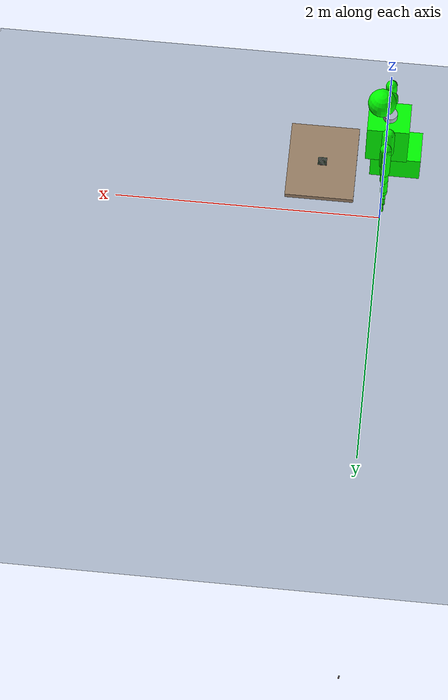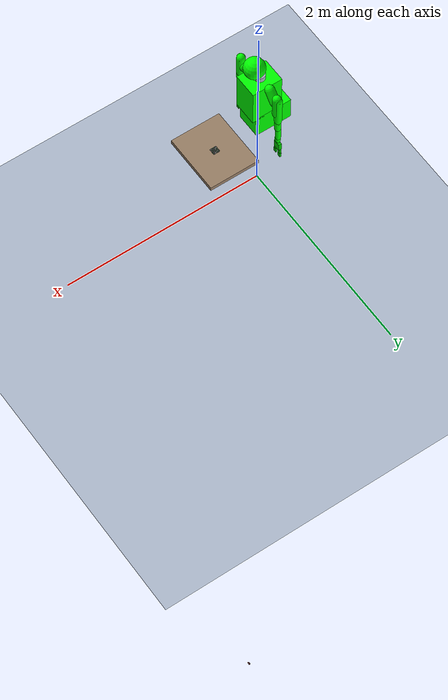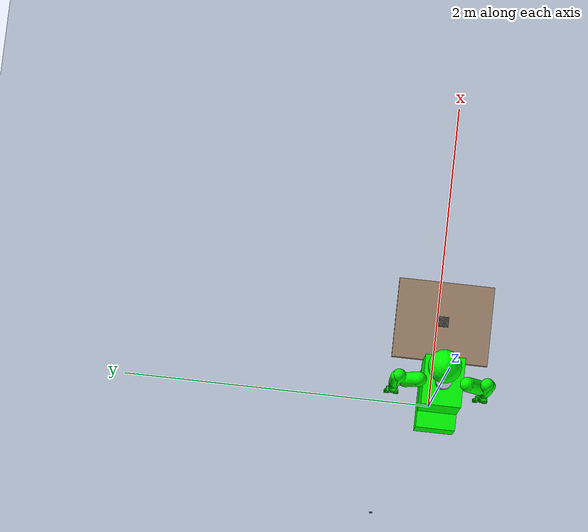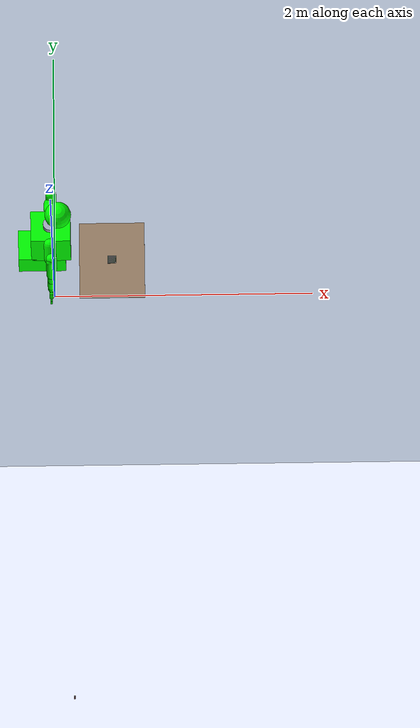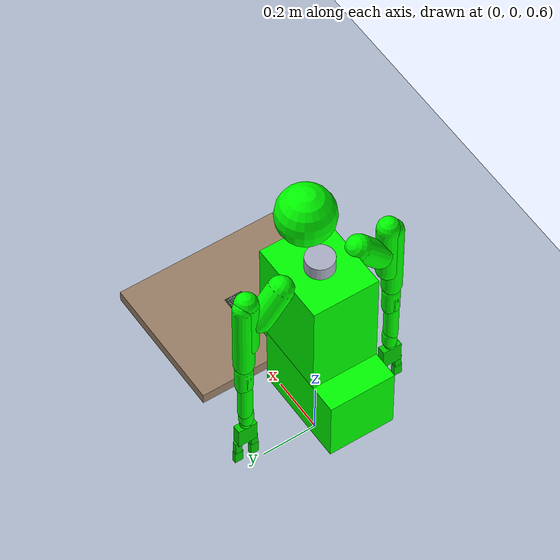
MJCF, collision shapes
<mujoco model="alex_lego_episode">
    <compiler meshdir="../robots/alex/" balanceinertia="true" />
    <include file="../robots/alex/alex.xml" />
    <option timestep="0.002" gravity="0 0 -9.81" integrator="implicitfast" cone="pyramidal" solver="Newton" iterations="80" ls_iterations="10">
        <flag energy="enable" />
    </option>
    <default>
        <default class="lego/stud">
            <geom contype="6" conaffinity="7" solref="0.003 1.0" solimp="0.97 0.995 0.001 0.5 4" friction="0.65 0.005 0.005" condim="4" />
        </default>
        <default class="lego/tube">
            <geom contype="4" conaffinity="4" solref="0.003 1.0" solimp="0.97 0.995 0.001 0.5 4" friction="0.65 0.005 0.005" condim="4" />
        </default>
        <default class="lego/brick_surface">
            <geom contype="2" conaffinity="3" solref="0.005 1.0" solimp="0.9 0.95 0.001 0.5 2" friction="0.4 0.005 0.002" condim="3" />
        </default>
        <default class="lego/baseplate">
            <geom contype="2" conaffinity="3" solref="0.005 1.0" solimp="0.9 0.95 0.001 0.5 2" friction="0.6 0.01 0.005" condim="3" />
        </default>
    </default>
    <statistic center="0 0 1.0" extent="1.5" />
    <visual>
        <headlight diffuse="0.6 0.6 0.6" ambient="0.3 0.3 0.3" specular="0 0 0" />
        <rgba haze="0.15 0.25 0.35 1" />
        <global azimuth="120" elevation="-20" offwidth="1280" offheight="720" />
    </visual>
    <asset>
        <texture type="2d" name="groundplane" builtin="checker" rgb1="0.2 0.3 0.4" rgb2="0.1 0.2 0.3" width="300" height="300" />
        <material name="groundplane" texture="groundplane" texuniform="true" texrepeat="5 5" />
        <material name="table_wood" rgba="0.6 0.5 0.4 1" />
    </asset>
    <worldbody>
        <light pos="0 0 3" dir="0 0 -1" directional="true" />
        <camera name="overhead" pos="0 -2 2" xyaxes="1 0 0 0 0.7 0.7" />
        <camera name="third_person" pos="2.0 -1.3 1.7" xyaxes="0.55 0.83 0 -0.25 0.17 0.95" fovy="60" />
        <camera name="workspace_closeup" pos="0.6 -0.25 1.05" xyaxes="0.85 0.53 0 -0.22 0.35 0.91" fovy="50" />
        <geom name="floor" type="plane" size="0 0 0.05" material="groundplane" contype="1" conaffinity="1" priority="1" friction="0.8" condim="3" />
        <body name="table" pos="0.45 0 0.75">
            <geom type="box" size="0.25 0.3 0.02" material="table_wood" contype="1" conaffinity="1" friction="0.6" mass="10" />
        </body>
        <body name="baseplate_8x8" pos="0.45 0 0.77">
            <inertial pos="0 0 0.0016" mass="0.015744" diaginertia="0.0000053538 0.0000053538 0.0000106808" />
            <geom class="lego/baseplate" name="baseplate_8x8_surface" type="box" size="0.0319 0.0319 0.0016" pos="0 0 0.0016" group="3" />
            <geom name="baseplate_8x8_surface_vis" type="box" size="0.0319 0.0319 0.0016" pos="0 0 0.0016" group="0" contype="0" conaffinity="0" rgba="0.16 0.5 0.16 1" />
            <geom class="lego/stud" name="baseplate_8x8_stud_0_0" type="cylinder" size="0.00235 0.00085" pos="-0.028 -0.028 0.00405" group="3" />
            <geom name="baseplate_8x8_stud_0_0_vis" type="cylinder" size="0.0024 0.00085" pos="-0.028 -0.028 0.00405" group="0" contype="0" conaffinity="0" rgba="0.16 0.5 0.16 1" />
            <geom class="lego/stud" name="baseplate_8x8_stud_0_1" type="cylinder" size="0.00235 0.00085" pos="-0.028 -0.02 0.00405" group="3" />
            <geom name="baseplate_8x8_stud_0_1_vis" type="cylinder" size="0.0024 0.00085" pos="-0.028 -0.02 0.00405" group="0" contype="0" conaffinity="0" rgba="0.16 0.5 0.16 1" />
            <geom class="lego/stud" name="baseplate_8x8_stud_0_2" type="cylinder" size="0.00235 0.00085" pos="-0.028 -0.012 0.00405" group="3" />
            <geom name="baseplate_8x8_stud_0_2_vis" type="cylinder" size="0.0024 0.00085" pos="-0.028 -0.012 0.00405" group="0" contype="0" conaffinity="0" rgba="0.16 0.5 0.16 1" />
            <geom class="lego/stud" name="baseplate_8x8_stud_0_3" type="cylinder" size="0.00235 0.00085" pos="-0.028 -0.004 0.00405" group="3" />
            <geom name="baseplate_8x8_stud_0_3_vis" type="cylinder" size="0.0024 0.00085" pos="-0.028 -0.004 0.00405" group="0" contype="0" conaffinity="0" rgba="0.16 0.5 0.16 1" />
            <geom class="lego/stud" name="baseplate_8x8_stud_0_4" type="cylinder" size="0.00235 0.00085" pos="-0.028 0.004 0.00405" group="3" />
            <geom name="baseplate_8x8_stud_0_4_vis" type="cylinder" size="0.0024 0.00085" pos="-0.028 0.004 0.00405" group="0" contype="0" conaffinity="0" rgba="0.16 0.5 0.16 1" />
            <geom class="lego/stud" name="baseplate_8x8_stud_0_5" type="cylinder" size="0.00235 0.00085" pos="-0.028 0.012 0.00405" group="3" />
            <geom name="baseplate_8x8_stud_0_5_vis" type="cylinder" size="0.0024 0.00085" pos="-0.028 0.012 0.00405" group="0" contype="0" conaffinity="0" rgba="0.16 0.5 0.16 1" />
            <geom class="lego/stud" name="baseplate_8x8_stud_0_6" type="cylinder" size="0.00235 0.00085" pos="-0.028 0.02 0.00405" group="3" />
            <geom name="baseplate_8x8_stud_0_6_vis" type="cylinder" size="0.0024 0.00085" pos="-0.028 0.02 0.00405" group="0" contype="0" conaffinity="0" rgba="0.16 0.5 0.16 1" />
            <geom class="lego/stud" name="baseplate_8x8_stud_0_7" type="cylinder" size="0.00235 0.00085" pos="-0.028 0.028 0.00405" group="3" />
            <geom name="baseplate_8x8_stud_0_7_vis" type="cylinder" size="0.0024 0.00085" pos="-0.028 0.028 0.00405" group="0" contype="0" conaffinity="0" rgba="0.16 0.5 0.16 1" />
            <geom class="lego/stud" name="baseplate_8x8_stud_1_0" type="cylinder" size="0.00235 0.00085" pos="-0.02 -0.028 0.00405" group="3" />
            <geom name="baseplate_8x8_stud_1_0_vis" type="cylinder" size="0.0024 0.00085" pos="-0.02 -0.028 0.00405" group="0" contype="0" conaffinity="0" rgba="0.16 0.5 0.16 1" />
            <geom class="lego/stud" name="baseplate_8x8_stud_1_1" type="cylinder" size="0.00235 0.00085" pos="-0.02 -0.02 0.00405" group="3" />
            <geom name="baseplate_8x8_stud_1_1_vis" type="cylinder" size="0.0024 0.00085" pos="-0.02 -0.02 0.00405" group="0" contype="0" conaffinity="0" rgba="0.16 0.5 0.16 1" />
            <geom class="lego/stud" name="baseplate_8x8_stud_1_2" type="cylinder" size="0.00235 0.00085" pos="-0.02 -0.012 0.00405" group="3" />
            <geom name="baseplate_8x8_stud_1_2_vis" type="cylinder" size="0.0024 0.00085" pos="-0.02 -0.012 0.00405" group="0" contype="0" conaffinity="0" rgba="0.16 0.5 0.16 1" />
            <geom class="lego/stud" name="baseplate_8x8_stud_1_3" type="cylinder" size="0.00235 0.00085" pos="-0.02 -0.004 0.00405" group="3" />
            <geom name="baseplate_8x8_stud_1_3_vis" type="cylinder" size="0.0024 0.00085" pos="-0.02 -0.004 0.00405" group="0" contype="0" conaffinity="0" rgba="0.16 0.5 0.16 1" />
            <geom class="lego/stud" name="baseplate_8x8_stud_1_4" type="cylinder" size="0.00235 0.00085" pos="-0.02 0.004 0.00405" group="3" />
            <geom name="baseplate_8x8_stud_1_4_vis" type="cylinder" size="0.0024 0.00085" pos="-0.02 0.004 0.00405" group="0" contype="0" conaffinity="0" rgba="0.16 0.5 0.16 1" />
            <geom class="lego/stud" name="baseplate_8x8_stud_1_5" type="cylinder" size="0.00235 0.00085" pos="-0.02 0.012 0.00405" group="3" />
            <geom name="baseplate_8x8_stud_1_5_vis" type="cylinder" size="0.0024 0.00085" pos="-0.02 0.012 0.00405" group="0" contype="0" conaffinity="0" rgba="0.16 0.5 0.16 1" />
            <geom class="lego/stud" name="baseplate_8x8_stud_1_6" type="cylinder" size="0.00235 0.00085" pos="-0.02 0.02 0.00405" group="3" />
            <geom name="baseplate_8x8_stud_1_6_vis" type="cylinder" size="0.0024 0.00085" pos="-0.02 0.02 0.00405" group="0" contype="0" conaffinity="0" rgba="0.16 0.5 0.16 1" />
            <geom class="lego/stud" name="baseplate_8x8_stud_1_7" type="cylinder" size="0.00235 0.00085" pos="-0.02 0.028 0.00405" group="3" />
            <geom name="baseplate_8x8_stud_1_7_vis" type="cylinder" size="0.0024 0.00085" pos="-0.02 0.028 0.00405" group="0" contype="0" conaffinity="0" rgba="0.16 0.5 0.16 1" />
            <geom class="lego/stud" name="baseplate_8x8_stud_2_0" type="cylinder" size="0.00235 0.00085" pos="-0.012 -0.028 0.00405" group="3" />
            <geom name="baseplate_8x8_stud_2_0_vis" type="cylinder" size="0.0024 0.00085" pos="-0.012 -0.028 0.00405" group="0" contype="0" conaffinity="0" rgba="0.16 0.5 0.16 1" />
            <geom class="lego/stud" name="baseplate_8x8_stud_2_1" type="cylinder" size="0.00235 0.00085" pos="-0.012 -0.02 0.00405" group="3" />
            <geom name="baseplate_8x8_stud_2_1_vis" type="cylinder" size="0.0024 0.00085" pos="-0.012 -0.02 0.00405" group="0" contype="0" conaffinity="0" rgba="0.16 0.5 0.16 1" />
            <geom class="lego/stud" name="baseplate_8x8_stud_2_2" type="cylinder" size="0.00235 0.00085" pos="-0.012 -0.012 0.00405" group="3" />
            <geom name="baseplate_8x8_stud_2_2_vis" type="cylinder" size="0.0024 0.00085" pos="-0.012 -0.012 0.00405" group="0" contype="0" conaffinity="0" rgba="0.16 0.5 0.16 1" />
            <geom class="lego/stud" name="baseplate_8x8_stud_2_3" type="cylinder" size="0.00235 0.00085" pos="-0.012 -0.004 0.00405" group="3" />
            <geom name="baseplate_8x8_stud_2_3_vis" type="cylinder" size="0.0024 0.00085" pos="-0.012 -0.004 0.00405" group="0" contype="0" conaffinity="0" rgba="0.16 0.5 0.16 1" />
            <geom class="lego/stud" name="baseplate_8x8_stud_2_4" type="cylinder" size="0.00235 0.00085" pos="-0.012 0.004 0.00405" group="3" />
            <geom name="baseplate_8x8_stud_2_4_vis" type="cylinder" size="0.0024 0.00085" pos="-0.012 0.004 0.00405" group="0" contype="0" conaffinity="0" rgba="0.16 0.5 0.16 1" />
            <geom class="lego/stud" name="baseplate_8x8_stud_2_5" type="cylinder" size="0.00235 0.00085" pos="-0.012 0.012 0.00405" group="3" />
            <geom name="baseplate_8x8_stud_2_5_vis" type="cylinder" size="0.0024 0.00085" pos="-0.012 0.012 0.00405" group="0" contype="0" conaffinity="0" rgba="0.16 0.5 0.16 1" />
            <geom class="lego/stud" name="baseplate_8x8_stud_2_6" type="cylinder" size="0.00235 0.00085" pos="-0.012 0.02 0.00405" group="3" />
            <geom name="baseplate_8x8_stud_2_6_vis" type="cylinder" size="0.0024 0.00085" pos="-0.012 0.02 0.00405" group="0" contype="0" conaffinity="0" rgba="0.16 0.5 0.16 1" />
            <geom class="lego/stud" name="baseplate_8x8_stud_2_7" type="cylinder" size="0.00235 0.00085" pos="-0.012 0.028 0.00405" group="3" />
            <geom name="baseplate_8x8_stud_2_7_vis" type="cylinder" size="0.0024 0.00085" pos="-0.012 0.028 0.00405" group="0" contype="0" conaffinity="0" rgba="0.16 0.5 0.16 1" />
            <geom class="lego/stud" name="baseplate_8x8_stud_3_0" type="cylinder" size="0.00235 0.00085" pos="-0.004 -0.028 0.00405" group="3" />
            <geom name="baseplate_8x8_stud_3_0_vis" type="cylinder" size="0.0024 0.00085" pos="-0.004 -0.028 0.00405" group="0" contype="0" conaffinity="0" rgba="0.16 0.5 0.16 1" />
            <geom class="lego/stud" name="baseplate_8x8_stud_3_1" type="cylinder" size="0.00235 0.00085" pos="-0.004 -0.02 0.00405" group="3" />
            <geom name="baseplate_8x8_stud_3_1_vis" type="cylinder" size="0.0024 0.00085" pos="-0.004 -0.02 0.00405" group="0" contype="0" conaffinity="0" rgba="0.16 0.5 0.16 1" />
            <geom class="lego/stud" name="baseplate_8x8_stud_3_2" type="cylinder" size="0.00235 0.00085" pos="-0.004 -0.012 0.00405" group="3" />
            <geom name="baseplate_8x8_stud_3_2_vis" type="cylinder" size="0.0024 0.00085" pos="-0.004 -0.012 0.00405" group="0" contype="0" conaffinity="0" rgba="0.16 0.5 0.16 1" />
            <geom class="lego/stud" name="baseplate_8x8_stud_3_3" type="cylinder" size="0.00235 0.00085" pos="-0.004 -0.004 0.00405" group="3" />
            <geom name="baseplate_8x8_stud_3_3_vis" type="cylinder" size="0.0024 0.00085" pos="-0.004 -0.004 0.00405" group="0" contype="0" conaffinity="0" rgba="0.16 0.5 0.16 1" />
            <geom class="lego/stud" name="baseplate_8x8_stud_3_4" type="cylinder" size="0.00235 0.00085" pos="-0.004 0.004 0.00405" group="3" />
            <geom name="baseplate_8x8_stud_3_4_vis" type="cylinder" size="0.0024 0.00085" pos="-0.004 0.004 0.00405" group="0" contype="0" conaffinity="0" rgba="0.16 0.5 0.16 1" />
            <geom class="lego/stud" name="baseplate_8x8_stud_3_5" type="cylinder" size="0.00235 0.00085" pos="-0.004 0.012 0.00405" group="3" />
            <geom name="baseplate_8x8_stud_3_5_vis" type="cylinder" size="0.0024 0.00085" pos="-0.004 0.012 0.00405" group="0" contype="0" conaffinity="0" rgba="0.16 0.5 0.16 1" />
            <geom class="lego/stud" name="baseplate_8x8_stud_3_6" type="cylinder" size="0.00235 0.00085" pos="-0.004 0.02 0.00405" group="3" />
            <geom name="baseplate_8x8_stud_3_6_vis" type="cylinder" size="0.0024 0.00085" pos="-0.004 0.02 0.00405" group="0" contype="0" conaffinity="0" rgba="0.16 0.5 0.16 1" />
            <geom class="lego/stud" name="baseplate_8x8_stud_3_7" type="cylinder" size="0.00235 0.00085" pos="-0.004 0.028 0.00405" group="3" />
            <geom name="baseplate_8x8_stud_3_7_vis" type="cylinder" size="0.0024 0.00085" pos="-0.004 0.028 0.00405" group="0" contype="0" conaffinity="0" rgba="0.16 0.5 0.16 1" />
            <geom class="lego/stud" name="baseplate_8x8_stud_4_0" type="cylinder" size="0.00235 0.00085" pos="0.004 -0.028 0.00405" group="3" />
            <geom name="baseplate_8x8_stud_4_0_vis" type="cylinder" size="0.0024 0.00085" pos="0.004 -0.028 0.00405" group="0" contype="0" conaffinity="0" rgba="0.16 0.5 0.16 1" />
            <geom class="lego/stud" name="baseplate_8x8_stud_4_1" type="cylinder" size="0.00235 0.00085" pos="0.004 -0.02 0.00405" group="3" />
            <geom name="baseplate_8x8_stud_4_1_vis" type="cylinder" size="0.0024 0.00085" pos="0.004 -0.02 0.00405" group="0" contype="0" conaffinity="0" rgba="0.16 0.5 0.16 1" />
            <geom class="lego/stud" name="baseplate_8x8_stud_4_2" type="cylinder" size="0.00235 0.00085" pos="0.004 -0.012 0.00405" group="3" />
            <geom name="baseplate_8x8_stud_4_2_vis" type="cylinder" size="0.0024 0.00085" pos="0.004 -0.012 0.00405" group="0" contype="0" conaffinity="0" rgba="0.16 0.5 0.16 1" />
            <geom class="lego/stud" name="baseplate_8x8_stud_4_3" type="cylinder" size="0.00235 0.00085" pos="0.004 -0.004 0.00405" group="3" />
            <geom name="baseplate_8x8_stud_4_3_vis" type="cylinder" size="0.0024 0.00085" pos="0.004 -0.004 0.00405" group="0" contype="0" conaffinity="0" rgba="0.16 0.5 0.16 1" />
            <geom class="lego/stud" name="baseplate_8x8_stud_4_4" type="cylinder" size="0.00235 0.00085" pos="0.004 0.004 0.00405" group="3" />
            <geom name="baseplate_8x8_stud_4_4_vis" type="cylinder" size="0.0024 0.00085" pos="0.004 0.004 0.00405" group="0" contype="0" conaffinity="0" rgba="0.16 0.5 0.16 1" />
            <geom class="lego/stud" name="baseplate_8x8_stud_4_5" type="cylinder" size="0.00235 0.00085" pos="0.004 0.012 0.00405" group="3" />
            <geom name="baseplate_8x8_stud_4_5_vis" type="cylinder" size="0.0024 0.00085" pos="0.004 0.012 0.00405" group="0" contype="0" conaffinity="0" rgba="0.16 0.5 0.16 1" />
            <geom class="lego/stud" name="baseplate_8x8_stud_4_6" type="cylinder" size="0.00235 0.00085" pos="0.004 0.02 0.00405" group="3" />
            <geom name="baseplate_8x8_stud_4_6_vis" type="cylinder" size="0.0024 0.00085" pos="0.004 0.02 0.00405" group="0" contype="0" conaffinity="0" rgba="0.16 0.5 0.16 1" />
            <geom class="lego/stud" name="baseplate_8x8_stud_4_7" type="cylinder" size="0.00235 0.00085" pos="0.004 0.028 0.00405" group="3" />
            <geom name="baseplate_8x8_stud_4_7_vis" type="cylinder" size="0.0024 0.00085" pos="0.004 0.028 0.00405" group="0" contype="0" conaffinity="0" rgba="0.16 0.5 0.16 1" />
            <geom class="lego/stud" name="baseplate_8x8_stud_5_0" type="cylinder" size="0.00235 0.00085" pos="0.012 -0.028 0.00405" group="3" />
            <geom name="baseplate_8x8_stud_5_0_vis" type="cylinder" size="0.0024 0.00085" pos="0.012 -0.028 0.00405" group="0" contype="0" conaffinity="0" rgba="0.16 0.5 0.16 1" />
            <geom class="lego/stud" name="baseplate_8x8_stud_5_1" type="cylinder" size="0.00235 0.00085" pos="0.012 -0.02 0.00405" group="3" />
            <geom name="baseplate_8x8_stud_5_1_vis" type="cylinder" size="0.0024 0.00085" pos="0.012 -0.02 0.00405" group="0" contype="0" conaffinity="0" rgba="0.16 0.5 0.16 1" />
            <geom class="lego/stud" name="baseplate_8x8_stud_5_2" type="cylinder" size="0.00235 0.00085" pos="0.012 -0.012 0.00405" group="3" />
            <geom name="baseplate_8x8_stud_5_2_vis" type="cylinder" size="0.0024 0.00085" pos="0.012 -0.012 0.00405" group="0" contype="0" conaffinity="0" rgba="0.16 0.5 0.16 1" />
            <geom class="lego/stud" name="baseplate_8x8_stud_5_3" type="cylinder" size="0.00235 0.00085" pos="0.012 -0.004 0.00405" group="3" />
            <geom name="baseplate_8x8_stud_5_3_vis" type="cylinder" size="0.0024 0.00085" pos="0.012 -0.004 0.00405" group="0" contype="0" conaffinity="0" rgba="0.16 0.5 0.16 1" />
            <geom class="lego/stud" name="baseplate_8x8_stud_5_4" type="cylinder" size="0.00235 0.00085" pos="0.012 0.004 0.00405" group="3" />
            <geom name="baseplate_8x8_stud_5_4_vis" type="cylinder" size="0.0024 0.00085" pos="0.012 0.004 0.00405" group="0" contype="0" conaffinity="0" rgba="0.16 0.5 0.16 1" />
            <geom class="lego/stud" name="baseplate_8x8_stud_5_5" type="cylinder" size="0.00235 0.00085" pos="0.012 0.012 0.00405" group="3" />
            <geom name="baseplate_8x8_stud_5_5_vis" type="cylinder" size="0.0024 0.00085" pos="0.012 0.012 0.00405" group="0" contype="0" conaffinity="0" rgba="0.16 0.5 0.16 1" />
            <geom class="lego/stud" name="baseplate_8x8_stud_5_6" type="cylinder" size="0.00235 0.00085" pos="0.012 0.02 0.00405" group="3" />
            <geom name="baseplate_8x8_stud_5_6_vis" type="cylinder" size="0.0024 0.00085" pos="0.012 0.02 0.00405" group="0" contype="0" conaffinity="0" rgba="0.16 0.5 0.16 1" />
            <geom class="lego/stud" name="baseplate_8x8_stud_5_7" type="cylinder" size="0.00235 0.00085" pos="0.012 0.028 0.00405" group="3" />
            <geom name="baseplate_8x8_stud_5_7_vis" type="cylinder" size="0.0024 0.00085" pos="0.012 0.028 0.00405" group="0" contype="0" conaffinity="0" rgba="0.16 0.5 0.16 1" />
            <geom class="lego/stud" name="baseplate_8x8_stud_6_0" type="cylinder" size="0.00235 0.00085" pos="0.02 -0.028 0.00405" group="3" />
            <geom name="baseplate_8x8_stud_6_0_vis" type="cylinder" size="0.0024 0.00085" pos="0.02 -0.028 0.00405" group="0" contype="0" conaffinity="0" rgba="0.16 0.5 0.16 1" />
            <geom class="lego/stud" name="baseplate_8x8_stud_6_1" type="cylinder" size="0.00235 0.00085" pos="0.02 -0.02 0.00405" group="3" />
            <geom name="baseplate_8x8_stud_6_1_vis" type="cylinder" size="0.0024 0.00085" pos="0.02 -0.02 0.00405" group="0" contype="0" conaffinity="0" rgba="0.16 0.5 0.16 1" />
            <geom class="lego/stud" name="baseplate_8x8_stud_6_2" type="cylinder" size="0.00235 0.00085" pos="0.02 -0.012 0.00405" group="3" />
            <geom name="baseplate_8x8_stud_6_2_vis" type="cylinder" size="0.0024 0.00085" pos="0.02 -0.012 0.00405" group="0" contype="0" conaffinity="0" rgba="0.16 0.5 0.16 1" />
            <geom class="lego/stud" name="baseplate_8x8_stud_6_3" type="cylinder" size="0.00235 0.00085" pos="0.02 -0.004 0.00405" group="3" />
            <geom name="baseplate_8x8_stud_6_3_vis" type="cylinder" size="0.0024 0.00085" pos="0.02 -0.004 0.00405" group="0" contype="0" conaffinity="0" rgba="0.16 0.5 0.16 1" />
            <geom class="lego/stud" name="baseplate_8x8_stud_6_4" type="cylinder" size="0.00235 0.00085" pos="0.02 0.004 0.00405" group="3" />
            <geom name="baseplate_8x8_stud_6_4_vis" type="cylinder" size="0.0024 0.00085" pos="0.02 0.004 0.00405" group="0" contype="0" conaffinity="0" rgba="0.16 0.5 0.16 1" />
            <geom class="lego/stud" name="baseplate_8x8_stud_6_5" type="cylinder" size="0.00235 0.00085" pos="0.02 0.012 0.00405" group="3" />
            <geom name="baseplate_8x8_stud_6_5_vis" type="cylinder" size="0.0024 0.00085" pos="0.02 0.012 0.00405" group="0" contype="0" conaffinity="0" rgba="0.16 0.5 0.16 1" />
            <geom class="lego/stud" name="baseplate_8x8_stud_6_6" type="cylinder" size="0.00235 0.00085" pos="0.02 0.02 0.00405" group="3" />
            <geom name="baseplate_8x8_stud_6_6_vis" type="cylinder" size="0.0024 0.00085" pos="0.02 0.02 0.00405" group="0" contype="0" conaffinity="0" rgba="0.16 0.5 0.16 1" />
            <geom class="lego/stud" name="baseplate_8x8_stud_6_7" type="cylinder" size="0.00235 0.00085" pos="0.02 0.028 0.00405" group="3" />
            <geom name="baseplate_8x8_stud_6_7_vis" type="cylinder" size="0.0024 0.00085" pos="0.02 0.028 0.00405" group="0" contype="0" conaffinity="0" rgba="0.16 0.5 0.16 1" />
            <geom class="lego/stud" name="baseplate_8x8_stud_7_0" type="cylinder" size="0.00235 0.00085" pos="0.028 -0.028 0.00405" group="3" />
            <geom name="baseplate_8x8_stud_7_0_vis" type="cylinder" size="0.0024 0.00085" pos="0.028 -0.028 0.00405" group="0" contype="0" conaffinity="0" rgba="0.16 0.5 0.16 1" />
            <geom class="lego/stud" name="baseplate_8x8_stud_7_1" type="cylinder" size="0.00235 0.00085" pos="0.028 -0.02 0.00405" group="3" />
            <geom name="baseplate_8x8_stud_7_1_vis" type="cylinder" size="0.0024 0.00085" pos="0.028 -0.02 0.00405" group="0" contype="0" conaffinity="0" rgba="0.16 0.5 0.16 1" />
            <geom class="lego/stud" name="baseplate_8x8_stud_7_2" type="cylinder" size="0.00235 0.00085" pos="0.028 -0.012 0.00405" group="3" />
            <geom name="baseplate_8x8_stud_7_2_vis" type="cylinder" size="0.0024 0.00085" pos="0.028 -0.012 0.00405" group="0" contype="0" conaffinity="0" rgba="0.16 0.5 0.16 1" />
            <geom class="lego/stud" name="baseplate_8x8_stud_7_3" type="cylinder" size="0.00235 0.00085" pos="0.028 -0.004 0.00405" group="3" />
            <geom name="baseplate_8x8_stud_7_3_vis" type="cylinder" size="0.0024 0.00085" pos="0.028 -0.004 0.00405" group="0" contype="0" conaffinity="0" rgba="0.16 0.5 0.16 1" />
            <geom class="lego/stud" name="baseplate_8x8_stud_7_4" type="cylinder" size="0.00235 0.00085" pos="0.028 0.004 0.00405" group="3" />
            <geom name="baseplate_8x8_stud_7_4_vis" type="cylinder" size="0.0024 0.00085" pos="0.028 0.004 0.00405" group="0" contype="0" conaffinity="0" rgba="0.16 0.5 0.16 1" />
            <geom class="lego/stud" name="baseplate_8x8_stud_7_5" type="cylinder" size="0.00235 0.00085" pos="0.028 0.012 0.00405" group="3" />
            <geom name="baseplate_8x8_stud_7_5_vis" type="cylinder" size="0.0024 0.00085" pos="0.028 0.012 0.00405" group="0" contype="0" conaffinity="0" rgba="0.16 0.5 0.16 1" />
            <geom class="lego/stud" name="baseplate_8x8_stud_7_6" type="cylinder" size="0.00235 0.00085" pos="0.028 0.02 0.00405" group="3" />
            <geom name="baseplate_8x8_stud_7_6_vis" type="cylinder" size="0.0024 0.00085" pos="0.028 0.02 0.00405" group="0" contype="0" conaffinity="0" rgba="0.16 0.5 0.16 1" />
            <geom class="lego/stud" name="baseplate_8x8_stud_7_7" type="cylinder" size="0.00235 0.00085" pos="0.028 0.028 0.00405" group="3" />
            <geom name="baseplate_8x8_stud_7_7_vis" type="cylinder" size="0.0024 0.00085" pos="0.028 0.028 0.00405" group="0" contype="0" conaffinity="0" rgba="0.16 0.5 0.16 1" />
        </body>
        <body name="brick_0_2x2" pos="0 0 -10">
            <freejoint name="brick_0_2x2_joint" />
            <inertial pos="0 0 0.0048" mass="0.001057" diaginertia="0.0000000301 0.0000000301 0.000000044" />
            <geom class="lego/brick_surface" name="brick_0_2x2_shell_top" type="box" size="0.0079 0.0079 0.0005" pos="0 0 0.0091" group="3" />
            <geom class="lego/brick_surface" name="brick_0_2x2_shell_lx" type="box" size="0.0006 0.0079 0.0048" pos="-0.0073 0 0.0048" group="3" />
            <geom class="lego/brick_surface" name="brick_0_2x2_shell_rx" type="box" size="0.0006 0.0079 0.0048" pos="0.0073 0 0.0048" group="3" />
            <geom class="lego/brick_surface" name="brick_0_2x2_shell_fy" type="box" size="0.0067 0.0006 0.0048" pos="0 0.0073 0.0048" group="3" />
            <geom class="lego/brick_surface" name="brick_0_2x2_shell_by" type="box" size="0.0067 0.0006 0.0048" pos="0 -0.0073 0.0048" group="3" />
            <geom name="brick_0_2x2_shell_vis" type="box" size="0.0079 0.0079 0.0048" pos="0 0 0.0048" group="0" contype="0" conaffinity="0" rgba="0.78 0.09 0.09 1" />
            <geom class="lego/stud" name="brick_0_2x2_stud_0_0" type="cylinder" size="0.00235 0.00085" pos="-0.004 -0.004 0.01045" group="3" />
            <geom name="brick_0_2x2_stud_0_0_vis" type="cylinder" size="0.0024 0.00085" pos="-0.004 -0.004 0.01045" group="0" contype="0" conaffinity="0" rgba="0.78 0.09 0.09 1" />
            <geom class="lego/stud" name="brick_0_2x2_stud_0_1" type="cylinder" size="0.00235 0.00085" pos="-0.004 0.004 0.01045" group="3" />
            <geom name="brick_0_2x2_stud_0_1_vis" type="cylinder" size="0.0024 0.00085" pos="-0.004 0.004 0.01045" group="0" contype="0" conaffinity="0" rgba="0.78 0.09 0.09 1" />
            <geom class="lego/stud" name="brick_0_2x2_stud_1_0" type="cylinder" size="0.00235 0.00085" pos="0.004 -0.004 0.01045" group="3" />
            <geom name="brick_0_2x2_stud_1_0_vis" type="cylinder" size="0.0024 0.00085" pos="0.004 -0.004 0.01045" group="0" contype="0" conaffinity="0" rgba="0.78 0.09 0.09 1" />
            <geom class="lego/stud" name="brick_0_2x2_stud_1_1" type="cylinder" size="0.00235 0.00085" pos="0.004 0.004 0.01045" group="3" />
            <geom name="brick_0_2x2_stud_1_1_vis" type="cylinder" size="0.0024 0.00085" pos="0.004 0.004 0.01045" group="0" contype="0" conaffinity="0" rgba="0.78 0.09 0.09 1" />
            <geom class="lego/tube" name="brick_0_2x2_tube_0_c0" type="capsule" size="0.00055" fromto="0.003 0 0 0.003 0 0.0017" group="3" />
            <geom class="lego/tube" name="brick_0_2x2_tube_0_c1" type="capsule" size="0.00055" fromto="0.002121 0.002121 0 0.002121 0.002121 0.0017" group="3" />
            <geom class="lego/tube" name="brick_0_2x2_tube_0_c2" type="capsule" size="0.00055" fromto="0 0.003 0 0 0.003 0.0017" group="3" />
            <geom class="lego/tube" name="brick_0_2x2_tube_0_c3" type="capsule" size="0.00055" fromto="-0.002121 0.002121 0 -0.002121 0.002121 0.0017" group="3" />
            <geom class="lego/tube" name="brick_0_2x2_tube_0_c4" type="capsule" size="0.00055" fromto="-0.003 0 0 -0.003 0 0.0017" group="3" />
            <geom class="lego/tube" name="brick_0_2x2_tube_0_c5" type="capsule" size="0.00055" fromto="-0.002121 -0.002121 0 -0.002121 -0.002121 0.0017" group="3" />
            <geom class="lego/tube" name="brick_0_2x2_tube_0_c6" type="capsule" size="0.00055" fromto="-0 -0.003 0 -0 -0.003 0.0017" group="3" />
            <geom class="lego/tube" name="brick_0_2x2_tube_0_c7" type="capsule" size="0.00055" fromto="0.002121 -0.002121 0 0.002121 -0.002121 0.0017" group="3" />
        </body>
        <body name="brick_1_2x4" pos="0 0 -10">
            <freejoint name="brick_1_2x4_joint" />
            <inertial pos="0 0 0.0048" mass="0.001864" diaginertia="0.0000001714 0.0000000531 0.0000001959" />
            <geom class="lego/brick_surface" name="brick_1_2x4_shell_top" type="box" size="0.0079 0.0159 0.0005" pos="0 0 0.0091" group="3" />
            <geom class="lego/brick_surface" name="brick_1_2x4_shell_lx" type="box" size="0.0006 0.0159 0.0048" pos="-0.0073 0 0.0048" group="3" />
            <geom class="lego/brick_surface" name="brick_1_2x4_shell_rx" type="box" size="0.0006 0.0159 0.0048" pos="0.0073 0 0.0048" group="3" />
            <geom class="lego/brick_surface" name="brick_1_2x4_shell_fy" type="box" size="0.0067 0.0006 0.0048" pos="0 0.0153 0.0048" group="3" />
            <geom class="lego/brick_surface" name="brick_1_2x4_shell_by" type="box" size="0.0067 0.0006 0.0048" pos="0 -0.0153 0.0048" group="3" />
            <geom name="brick_1_2x4_shell_vis" type="box" size="0.0079 0.0159 0.0048" pos="0 0 0.0048" group="0" contype="0" conaffinity="0" rgba="0.78 0.09 0.09 1" />
            <geom class="lego/stud" name="brick_1_2x4_stud_0_0" type="cylinder" size="0.00235 0.00085" pos="-0.004 -0.012 0.01045" group="3" />
            <geom name="brick_1_2x4_stud_0_0_vis" type="cylinder" size="0.0024 0.00085" pos="-0.004 -0.012 0.01045" group="0" contype="0" conaffinity="0" rgba="0.78 0.09 0.09 1" />
            <geom class="lego/stud" name="brick_1_2x4_stud_0_1" type="cylinder" size="0.00235 0.00085" pos="-0.004 -0.004 0.01045" group="3" />
            <geom name="brick_1_2x4_stud_0_1_vis" type="cylinder" size="0.0024 0.00085" pos="-0.004 -0.004 0.01045" group="0" contype="0" conaffinity="0" rgba="0.78 0.09 0.09 1" />
            <geom class="lego/stud" name="brick_1_2x4_stud_0_2" type="cylinder" size="0.00235 0.00085" pos="-0.004 0.004 0.01045" group="3" />
            <geom name="brick_1_2x4_stud_0_2_vis" type="cylinder" size="0.0024 0.00085" pos="-0.004 0.004 0.01045" group="0" contype="0" conaffinity="0" rgba="0.78 0.09 0.09 1" />
            <geom class="lego/stud" name="brick_1_2x4_stud_0_3" type="cylinder" size="0.00235 0.00085" pos="-0.004 0.012 0.01045" group="3" />
            <geom name="brick_1_2x4_stud_0_3_vis" type="cylinder" size="0.0024 0.00085" pos="-0.004 0.012 0.01045" group="0" contype="0" conaffinity="0" rgba="0.78 0.09 0.09 1" />
            <geom class="lego/stud" name="brick_1_2x4_stud_1_0" type="cylinder" size="0.00235 0.00085" pos="0.004 -0.012 0.01045" group="3" />
            <geom name="brick_1_2x4_stud_1_0_vis" type="cylinder" size="0.0024 0.00085" pos="0.004 -0.012 0.01045" group="0" contype="0" conaffinity="0" rgba="0.78 0.09 0.09 1" />
            <geom class="lego/stud" name="brick_1_2x4_stud_1_1" type="cylinder" size="0.00235 0.00085" pos="0.004 -0.004 0.01045" group="3" />
            <geom name="brick_1_2x4_stud_1_1_vis" type="cylinder" size="0.0024 0.00085" pos="0.004 -0.004 0.01045" group="0" contype="0" conaffinity="0" rgba="0.78 0.09 0.09 1" />
            <geom class="lego/stud" name="brick_1_2x4_stud_1_2" type="cylinder" size="0.00235 0.00085" pos="0.004 0.004 0.01045" group="3" />
            <geom name="brick_1_2x4_stud_1_2_vis" type="cylinder" size="0.0024 0.00085" pos="0.004 0.004 0.01045" group="0" contype="0" conaffinity="0" rgba="0.78 0.09 0.09 1" />
            <geom class="lego/stud" name="brick_1_2x4_stud_1_3" type="cylinder" size="0.00235 0.00085" pos="0.004 0.012 0.01045" group="3" />
            <geom name="brick_1_2x4_stud_1_3_vis" type="cylinder" size="0.0024 0.00085" pos="0.004 0.012 0.01045" group="0" contype="0" conaffinity="0" rgba="0.78 0.09 0.09 1" />
            <geom class="lego/tube" name="brick_1_2x4_tube_0_c0" type="capsule" size="0.00055" fromto="0.003 -0.008 0 0.003 -0.008 0.0017" group="3" />
            <geom class="lego/tube" name="brick_1_2x4_tube_0_c1" type="capsule" size="0.00055" fromto="0.002121 -0.005879 0 0.002121 -0.005879 0.0017" group="3" />
            <geom class="lego/tube" name="brick_1_2x4_tube_0_c2" type="capsule" size="0.00055" fromto="0 -0.005 0 0 -0.005 0.0017" group="3" />
            <geom class="lego/tube" name="brick_1_2x4_tube_0_c3" type="capsule" size="0.00055" fromto="-0.002121 -0.005879 0 -0.002121 -0.005879 0.0017" group="3" />
            <geom class="lego/tube" name="brick_1_2x4_tube_0_c4" type="capsule" size="0.00055" fromto="-0.003 -0.008 0 -0.003 -0.008 0.0017" group="3" />
            <geom class="lego/tube" name="brick_1_2x4_tube_0_c5" type="capsule" size="0.00055" fromto="-0.002121 -0.010121 0 -0.002121 -0.010121 0.0017" group="3" />
            <geom class="lego/tube" name="brick_1_2x4_tube_0_c6" type="capsule" size="0.00055" fromto="-0 -0.011 0 -0 -0.011 0.0017" group="3" />
            <geom class="lego/tube" name="brick_1_2x4_tube_0_c7" type="capsule" size="0.00055" fromto="0.002121 -0.010121 0 0.002121 -0.010121 0.0017" group="3" />
            <geom class="lego/tube" name="brick_1_2x4_tube_1_c0" type="capsule" size="0.00055" fromto="0.003 0 0 0.003 0 0.0017" group="3" />
            <geom class="lego/tube" name="brick_1_2x4_tube_1_c1" type="capsule" size="0.00055" fromto="0.002121 0.002121 0 0.002121 0.002121 0.0017" group="3" />
            <geom class="lego/tube" name="brick_1_2x4_tube_1_c2" type="capsule" size="0.00055" fromto="0 0.003 0 0 0.003 0.0017" group="3" />
            <geom class="lego/tube" name="brick_1_2x4_tube_1_c3" type="capsule" size="0.00055" fromto="-0.002121 0.002121 0 -0.002121 0.002121 0.0017" group="3" />
            <geom class="lego/tube" name="brick_1_2x4_tube_1_c4" type="capsule" size="0.00055" fromto="-0.003 0 0 -0.003 0 0.0017" group="3" />
            <geom class="lego/tube" name="brick_1_2x4_tube_1_c5" type="capsule" size="0.00055" fromto="-0.002121 -0.002121 0 -0.002121 -0.002121 0.0017" group="3" />
            <geom class="lego/tube" name="brick_1_2x4_tube_1_c6" type="capsule" size="0.00055" fromto="-0 -0.003 0 -0 -0.003 0.0017" group="3" />
            <geom class="lego/tube" name="brick_1_2x4_tube_1_c7" type="capsule" size="0.00055" fromto="0.002121 -0.002121 0 0.002121 -0.002121 0.0017" group="3" />
            <geom class="lego/tube" name="brick_1_2x4_tube_2_c0" type="capsule" size="0.00055" fromto="0.003 0.008 0 0.003 0.008 0.0017" group="3" />
            <geom class="lego/tube" name="brick_1_2x4_tube_2_c1" type="capsule" size="0.00055" fromto="0.002121 0.010121 0 0.002121 0.010121 0.0017" group="3" />
            <geom class="lego/tube" name="brick_1_2x4_tube_2_c2" type="capsule" size="0.00055" fromto="0 0.011 0 0 0.011 0.0017" group="3" />
            <geom class="lego/tube" name="brick_1_2x4_tube_2_c3" type="capsule" size="0.00055" fromto="-0.002121 0.010121 0 -0.002121 0.010121 0.0017" group="3" />
            <geom class="lego/tube" name="brick_1_2x4_tube_2_c4" type="capsule" size="0.00055" fromto="-0.003 0.008 0 -0.003 0.008 0.0017" group="3" />
            <geom class="lego/tube" name="brick_1_2x4_tube_2_c5" type="capsule" size="0.00055" fromto="-0.002121 0.005879 0 -0.002121 0.005879 0.0017" group="3" />
            <geom class="lego/tube" name="brick_1_2x4_tube_2_c6" type="capsule" size="0.00055" fromto="-0 0.005 0 -0 0.005 0.0017" group="3" />
            <geom class="lego/tube" name="brick_1_2x4_tube_2_c7" type="capsule" size="0.00055" fromto="0.002121 0.005879 0 0.002121 0.005879 0.0017" group="3" />
        </body>
        <body name="brick_2_2x2" pos="0 0 -10">
            <freejoint name="brick_2_2x2_joint" />
            <inertial pos="0 0 0.0048" mass="0.001057" diaginertia="0.0000000301 0.0000000301 0.000000044" />
            <geom class="lego/brick_surface" name="brick_2_2x2_shell_top" type="box" size="0.0079 0.0079 0.0005" pos="0 0 0.0091" group="3" />
            <geom class="lego/brick_surface" name="brick_2_2x2_shell_lx" type="box" size="0.0006 0.0079 0.0048" pos="-0.0073 0 0.0048" group="3" />
            <geom class="lego/brick_surface" name="brick_2_2x2_shell_rx" type="box" size="0.0006 0.0079 0.0048" pos="0.0073 0 0.0048" group="3" />
            <geom class="lego/brick_surface" name="brick_2_2x2_shell_fy" type="box" size="0.0067 0.0006 0.0048" pos="0 0.0073 0.0048" group="3" />
            <geom class="lego/brick_surface" name="brick_2_2x2_shell_by" type="box" size="0.0067 0.0006 0.0048" pos="0 -0.0073 0.0048" group="3" />
            <geom name="brick_2_2x2_shell_vis" type="box" size="0.0079 0.0079 0.0048" pos="0 0 0.0048" group="0" contype="0" conaffinity="0" rgba="0.78 0.09 0.09 1" />
            <geom class="lego/stud" name="brick_2_2x2_stud_0_0" type="cylinder" size="0.00235 0.00085" pos="-0.004 -0.004 0.01045" group="3" />
            <geom name="brick_2_2x2_stud_0_0_vis" type="cylinder" size="0.0024 0.00085" pos="-0.004 -0.004 0.01045" group="0" contype="0" conaffinity="0" rgba="0.78 0.09 0.09 1" />
            <geom class="lego/stud" name="brick_2_2x2_stud_0_1" type="cylinder" size="0.00235 0.00085" pos="-0.004 0.004 0.01045" group="3" />
            <geom name="brick_2_2x2_stud_0_1_vis" type="cylinder" size="0.0024 0.00085" pos="-0.004 0.004 0.01045" group="0" contype="0" conaffinity="0" rgba="0.78 0.09 0.09 1" />
            <geom class="lego/stud" name="brick_2_2x2_stud_1_0" type="cylinder" size="0.00235 0.00085" pos="0.004 -0.004 0.01045" group="3" />
            <geom name="brick_2_2x2_stud_1_0_vis" type="cylinder" size="0.0024 0.00085" pos="0.004 -0.004 0.01045" group="0" contype="0" conaffinity="0" rgba="0.78 0.09 0.09 1" />
            <geom class="lego/stud" name="brick_2_2x2_stud_1_1" type="cylinder" size="0.00235 0.00085" pos="0.004 0.004 0.01045" group="3" />
            <geom name="brick_2_2x2_stud_1_1_vis" type="cylinder" size="0.0024 0.00085" pos="0.004 0.004 0.01045" group="0" contype="0" conaffinity="0" rgba="0.78 0.09 0.09 1" />
            <geom class="lego/tube" name="brick_2_2x2_tube_0_c0" type="capsule" size="0.00055" fromto="0.003 0 0 0.003 0 0.0017" group="3" />
            <geom class="lego/tube" name="brick_2_2x2_tube_0_c1" type="capsule" size="0.00055" fromto="0.002121 0.002121 0 0.002121 0.002121 0.0017" group="3" />
            <geom class="lego/tube" name="brick_2_2x2_tube_0_c2" type="capsule" size="0.00055" fromto="0 0.003 0 0 0.003 0.0017" group="3" />
            <geom class="lego/tube" name="brick_2_2x2_tube_0_c3" type="capsule" size="0.00055" fromto="-0.002121 0.002121 0 -0.002121 0.002121 0.0017" group="3" />
            <geom class="lego/tube" name="brick_2_2x2_tube_0_c4" type="capsule" size="0.00055" fromto="-0.003 0 0 -0.003 0 0.0017" group="3" />
            <geom class="lego/tube" name="brick_2_2x2_tube_0_c5" type="capsule" size="0.00055" fromto="-0.002121 -0.002121 0 -0.002121 -0.002121 0.0017" group="3" />
            <geom class="lego/tube" name="brick_2_2x2_tube_0_c6" type="capsule" size="0.00055" fromto="-0 -0.003 0 -0 -0.003 0.0017" group="3" />
            <geom class="lego/tube" name="brick_2_2x2_tube_0_c7" type="capsule" size="0.00055" fromto="0.002121 -0.002121 0 0.002121 -0.002121 0.0017" group="3" />
        </body>
    </worldbody>
    <keyframe>
        <key name="home" qpos="0 0 0 0 0 0 0 0 0 0 0 0 0 0 0 0 0 0 0 0 0 0 0 0 0 -10 1 0 0 0 0 0 -10 1 0 0 0 0 0 -10 1 0 0 0" ctrl="0 0 0 0 0 0 0 0 0 0 0 0 0 0 0 0 0" />
    </keyframe>
</mujoco>

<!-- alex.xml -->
<mujoco model="alex_upper_body">

    <compiler angle="radian" eulerseq="XYZ" autolimits="true"
              balanceinertia="true"/>

    <option iterations="50" ls_iterations="10" timestep="0.002" integrator="implicitfast">
        <flag energy="enable"/>
    </option>

    <default>
        <default class="alex">
            <joint damping="2" frictionloss="0.3"/>
            <position inheritrange="1"/>
            <default class="alex/spine">
                <joint axis="0 0 1" range="-0.5235987756 0.5235987756"
                       armature="0.01" damping="2.0" frictionloss="0.3"/>
                <position forcerange="-150 150" kp="112"/>
            </default>
            <default class="alex/shoulder">
                <default class="alex/shoulder/y">
                    <joint axis="0 1 0" range="-3.141592 1.22173"
                           armature="0.01" damping="2.0" frictionloss="0.3"/>
                    <position forcerange="-150 150" kp="112.5"/>
                </default>
                <default class="alex/shoulder/x">
                    <joint axis="1 0 0" armature="0.01" damping="2.0" frictionloss="0.3"/>
                    <position forcerange="-100 100" kp="75"/>
                    <default class="alex/shoulder/x/left">
                        <joint range="-0.349066 2.79253"/>
                    </default>
                    <default class="alex/shoulder/x/right">
                        <joint range="-2.79253 0.349066"/>
                    </default>
                </default>
                <default class="alex/shoulder/z">
                    <joint axis="0 0 1" armature="0.01" damping="1.5" frictionloss="0.2"/>
                    <position forcerange="-80 80" kp="60"/>
                    <default class="alex/shoulder/z/left">
                        <joint range="-1.91986 1.22173"/>
                    </default>
                    <default class="alex/shoulder/z/right">
                        <joint range="-1.22173 1.91986"/>
                    </default>
                </default>
            </default>
            <default class="alex/elbow">
                <joint axis="0 1 0" range="-2.35619 0.174532925"
                       armature="0.01" damping="1.5" frictionloss="0.2"/>
                <position forcerange="-80 80" kp="60"/>
            </default>
            <default class="alex/wrist">
                <position forcerange="-20 20" kp="15"/>
                <default class="alex/wrist/z">
                    <joint axis="0 0 1" range="-2.61799 2.61799"
                           armature="0.01" damping="0.5" frictionloss="0.1"/>
                </default>
                <default class="alex/wrist/x">
                    <joint axis="1 0 0" armature="0.01" damping="0.5" frictionloss="0.1"/>
                    <default class="alex/wrist/x/left">
                        <joint range="-1.8326 0.610865"/>
                    </default>
                    <default class="alex/wrist/x/right">
                        <joint range="-0.610865 1.8326"/>
                    </default>
                </default>
            </default>
            <default class="alex/gripper">
                <joint axis="0 0 1" range="-2.61799 2.61799"
                       armature="0.01" damping="0.3" frictionloss="0.05"/>
                <position forcerange="-20 20" kp="15"/>
            </default>
            <default class="alex/visual">
                <geom contype="0" conaffinity="0" group="1" type="mesh"/>
            </default>
            <default class="alex/collision">
                <geom group="3" contype="1" conaffinity="1" rgba="0 1 0 0.3"
                      solref="0.005 1.0" solimp="0.9 0.95 0.001 0.5 2"/>
            </default>
            <!-- EZGripper Gen2 defaults -->
            <default class="alex/ezgripper">
                <default class="alex/ezgripper/knuckle">
                    <joint axis="0 1 0" range="0 1.94" armature="0.005"
                           damping="0.2" frictionloss="0.02"/>
                    <position forcerange="-8 8" kp="10" inheritrange="1"/>
                </default>
                <default class="alex/ezgripper/collision">
                    <geom group="3" contype="1" conaffinity="1" rgba="0 0.8 0 0.3"
                          friction="1.5 0.02 0.01"
                          solref="0.005 1.0" solimp="0.9 0.95 0.001 0.5 2"/>
                </default>
                <default class="alex/ezgripper/visual">
                    <geom contype="0" conaffinity="0" group="1" type="mesh"/>
                </default>
            </default>
        </default>
    </default>

    <asset>
        <material name="gray" rgba="0.671705 0.692426 0.774270 1"/>
        <mesh name="pelvis" file="meshes/Pelvis.obj"/>
        <mesh name="torso" file="meshes/torso.obj"/>
        <mesh name="head" file="meshes/ALX02_01_A02_HeadLink.obj"/>
        <mesh name="left_shoulder_y" file="meshes/LeftShoulderPitchLink.obj"/>
        <mesh name="left_shoulder_x" file="meshes/LeftShoulderRollLink_longBicep.obj"/>
        <mesh name="left_shoulder_z" file="meshes/LeftShoulderYawLink.obj"/>
        <mesh name="left_elbow_y" file="meshes/LEFT_ELBOW_PITCH_LINK_413mm_LENGTH.obj"/>
        <mesh name="left_wrist_z" file="meshes/LeftWristYawLink.obj"/>
        <mesh name="left_wrist_x" file="meshes/LeftWristRollLink.obj"/>
        <mesh name="left_gripper" file="meshes/nub.obj"/>
        <mesh name="right_shoulder_y" file="meshes/RightShoulderPitchLink.obj"/>
        <mesh name="right_shoulder_x" file="meshes/RightShoulderRollLink_longBicep.obj"/>
        <mesh name="right_shoulder_z" file="meshes/RightShoulderYawLink.obj"/>
        <mesh name="right_elbow_y" file="meshes/RIGHT_ELBOW_PITCH_LINK_413mm_LENGTH.obj"/>
        <mesh name="right_wrist_z" file="meshes/RightWristYawLink.obj"/>
        <mesh name="right_wrist_x" file="meshes/RightWristRollLink.obj"/>
        <mesh name="right_gripper" file="meshes/nub.obj"/>
        <!-- EZGripper Gen2 meshes -->
        <mesh name="ezgripper_palm" file="meshes/SAKE_Palm_Dual_Gen2.stl"/>
        <mesh name="ezgripper_finger_l1" file="meshes/SAKE_Finger_L1_Gen2.stl"/>
        <mesh name="ezgripper_finger_l2" file="meshes/SAKE_Finger_L2_Gen2.stl"/>
    </asset>

    <worldbody>
        <body name="base_link" pos="0.0 0.0 1.0" childclass="alex">
            <!-- No inertial needed: base_link is fixed to world (no joint) -->
            <geom mesh="pelvis" material="gray" class="alex/visual"/>
            <geom name="base_collision" type="box" size="0.18 0.12 0.12"
                  pos="-0.08 0 -0.03" class="alex/collision"/>

            <body name="torso" pos="0.0 0 0.018">
                <inertial
                    pos="-0.014 0.001 0.326"
                    mass="11.478322779"
                    fullinertia="0.1764967124 0.1237602 0.1109598365 2.329659e-05 0.00830355822 0.00072436338"
                />
                <joint name="spine_z" class="alex/spine"/>
                <geom mesh="torso" pos="0.0 0.0 0.105063" material="gray" class="alex/visual"/>
                <geom name="torso_collision" type="box" size="0.15 0.12 0.20"
                      pos="-0.01 0 0.25" class="alex/collision"/>

                <!-- ==================== LEFT ARM ==================== -->
                <body name="left_shoulder_y" pos="-0.015 0.115474 0.352984" euler="0.698132 0.0 0.0">
                    <inertial
                        pos="-0.00264 0.12135 -0.006824"
                        mass="3.0331992"
                        fullinertia="0.01114656 0.00699715 0.0099942 0.00024166 0.0001507 0.00308767"
                    />
                    <joint name="left_shoulder_y" class="alex/shoulder/y"/>
                    <geom mesh="left_shoulder_y" material="gray" class="alex/visual"/>
                    <geom name="left_shoulder_y_collision" type="capsule"
                          size="0.045 0.06" pos="0 0.08 -0.01" class="alex/collision"/>

                    <body name="left_shoulder_x" pos="0.0 0.15676000 -0.01300000" euler="-0.698132 0.0 0.0">
                        <inertial
                            pos="0.01053 0.02124 -0.1052690"
                            mass="1.16160776"
                            fullinertia="0.00786831 0.00727049 0.0018045 0.00016417 -0.00075696 0.00099239"
                        />
                        <joint name="left_shoulder_x" class="alex/shoulder/x/left"/>
                        <geom mesh="left_shoulder_x" material="gray" class="alex/visual"/>
                        <geom name="left_shoulder_x_collision" type="capsule"
                              size="0.04 0.10" pos="0.01 0.02 -0.10"
                              euler="0 0 0" class="alex/collision"/>

                        <body name="left_shoulder_z" pos="0.0 0.035 0.0">
                            <inertial
                                pos="0.00510403 0.00274 -0.21745"
                                mass="3.134"
                                fullinertia="0.02661157 0.02633278 0.00308445 2.97e-06 0.00147256 0.00039997"
                            />
                            <joint name="left_shoulder_z" class="alex/shoulder/z/left"/>
                            <geom mesh="left_shoulder_z" pos="0.0 0.0 0.0867" material="gray" class="alex/visual"/>
                            <geom name="left_shoulder_z_collision" type="capsule"
                                  size="0.035 0.14" pos="0.005 0 -0.15"
                                  class="alex/collision"/>

                            <body name="left_elbow_y" pos="0.015 0.0 -0.3127">
                                <inertial
                                    pos="-0.01180322 -0.0035763 -0.04946747"
                                    mass="0.45"
                                    fullinertia="0.0008940385 0.0002691585 0.0002478294 0.0004472422 0.0003653737 0.0001357858"
                                />
                                <joint name="left_elbow_y" class="alex/elbow"/>
                                <geom mesh="left_elbow_y" material="gray" class="alex/visual"/>
                                <geom name="left_elbow_y_collision" type="capsule"
                                      size="0.03 0.04" pos="-0.01 0 -0.05"
                                      class="alex/collision"/>

                                <body name="left_wrist_z" pos="-0.015 0.0 0.0">
                                    <inertial
                                        pos="-0.00263832 -0.00050534 -0.13018376"
                                        mass="1.547"
                                        fullinertia="0.004662587 0.001803105 0.0002966306 0.002825398 0.001028921 0.0006324909"
                                    />
                                    <joint name="left_wrist_z" class="alex/wrist/z"/>
                                    <geom mesh="left_wrist_z" material="gray" class="alex/visual"/>
                                    <geom name="left_wrist_z_collision" type="capsule"
                                          size="0.025 0.10" pos="0 0 -0.13"
                                          class="alex/collision"/>

                                    <body name="left_wrist_x" pos="0.0 -0.013 -0.25">
                                        <inertial
                                            pos="0.00004053 0.01038395 0.00035532"
                                            mass="0.909"
                                            fullinertia="0.0006553625 0.0001645745 0.0001827797 0.0003160572 0.000334132 0.0001635935"
                                        />
                                        <joint name="left_wrist_x" class="alex/wrist/x/left"/>
                                        <geom mesh="left_wrist_x" material="gray" class="alex/visual"/>
                                        <geom name="left_wrist_x_collision" type="capsule"
                                              size="0.025 0.02" pos="0 0.01 0"
                                              class="alex/collision"/>

                                        <body name="left_gripper" pos="0.0 0.013 -0.031">
                                            <inertial
                                                pos="-0.000217 -0.000349 0.009761"
                                                mass="0.251"
                                                fullinertia="8.862382e-05 3.167086e-05 7.770774e-06 5.132406e-05 2.139744e-05 1.195988e-05"
                                            />
                                            <joint name="left_gripper_z" class="alex/gripper"/>
                                            <geom name="left_gripper_collision" type="capsule"
                                                  size="0.02 0.02" pos="0 0 0.01"
                                                  class="alex/collision"/>
                                            <site name="left_ee_site" pos="0 0 0.03"
                                                  type="sphere" size="0.008" rgba="1 0 0 0.5" group="4"/>
                                            <!-- Left wrist camera: attached to gripper body,
                                                 looks along +Z (toward fingertips/workspace). -->
                                            <camera name="left_wrist_cam" pos="0 0 0"
                                                    xyaxes="1 0 0 0 -1 0" fovy="75"/>

                                            <!-- EZGripper Gen2 -->
                                            <!-- Adapter transform from IHMC URDF (verified via FK symmetry — 0.0 cm error) -->
                                            <body name="left_ezgripper_palm" pos="0 0 -0.02" euler="3.14159 1.5708 0">
                                                <inertial pos="0.04 0 0" mass="0.3"
                                                          diaginertia="0.0003 0.0005 0.0004"/>
                                                <geom mesh="ezgripper_palm" material="gray"
                                                      class="alex/ezgripper/visual"/>
                                                <geom name="left_palm_collision" type="box"
                                                      size="0.04 0.035 0.015" pos="0.04 0 0"
                                                      class="alex/ezgripper/collision"/>
                                                <site name="left_tool_frame" pos="0.073 0 0"
                                                      type="sphere" size="0.005"
                                                      rgba="1 1 0 0.5" group="4"/>

                                                <!-- Finger 1 (primary, actuated) -->
                                                <body name="left_finger1_l1" pos="0.073 0.03 0">
                                                    <inertial pos="0.026 0 0" mass="0.025"
                                                              diaginertia="5e-06 2e-05 2e-05"/>
                                                    <joint name="left_knuckle_palm_l1_1"
                                                           class="alex/ezgripper/knuckle"/>
                                                    <geom mesh="ezgripper_finger_l1"
                                                          class="alex/ezgripper/visual"/>
                                                    <geom name="left_finger1_l1_col" type="box"
                                                          size="0.026 0.012 0.008" pos="0.026 0 0"
                                                          class="alex/ezgripper/collision"/>
                                                    <body name="left_finger1_l2" pos="0.052 0 0">
                                                        <inertial pos="0.02 0 0" mass="0.025"
                                                                  diaginertia="4e-06 1.5e-05 1.5e-05"/>
                                                        <joint name="left_knuckle_l1_l2_1"
                                                               class="alex/ezgripper/knuckle"/>
                                                        <geom mesh="ezgripper_finger_l2"
                                                              class="alex/ezgripper/visual"/>
                                                        <geom name="left_finger1_pad" type="box"
                                                              size="0.025 0.015 0.008" pos="0.02 0 0"
                                                              class="alex/ezgripper/collision"/>
                                                    </body>
                                                </body>

                                                <!-- Finger 2 (coupled to finger 1) -->
                                                <body name="left_finger2_l1" pos="0.073 -0.03 0">
                                                    <inertial pos="0.026 0 0" mass="0.025"
                                                              diaginertia="5e-06 2e-05 2e-05"/>
                                                    <joint name="left_knuckle_palm_l1_2"
                                                           class="alex/ezgripper/knuckle"/>
                                                    <geom mesh="ezgripper_finger_l1"
                                                          class="alex/ezgripper/visual"/>
                                                    <geom name="left_finger2_l1_col" type="box"
                                                          size="0.026 0.012 0.008" pos="0.026 0 0"
                                                          class="alex/ezgripper/collision"/>
                                                    <body name="left_finger2_l2" pos="0.052 0 0">
                                                        <inertial pos="0.02 0 0" mass="0.025"
                                                                  diaginertia="4e-06 1.5e-05 1.5e-05"/>
                                                        <joint name="left_knuckle_l1_l2_2"
                                                               class="alex/ezgripper/knuckle"/>
                                                        <geom mesh="ezgripper_finger_l2"
                                                              class="alex/ezgripper/visual"/>
                                                        <geom name="left_finger2_pad" type="box"
                                                              size="0.025 0.015 0.008" pos="0.02 0 0"
                                                              class="alex/ezgripper/collision"/>
                                                    </body>
                                                </body>
                                            </body>
                                        </body>
                                    </body>
                                </body>
                            </body>
                        </body>
                    </body>
                </body>

                <!-- ==================== NECK / HEAD (fixed) ==================== -->
                <body name="neck_z" pos="-0.015 0 0.450403">
                    <inertial
                        pos="0.00626571 0.0059834 0.15148116"
                        mass="1.03172573"
                        fullinertia="0.00611354 0.00602503 0.0009799 -5.224e-05 -0.00058532 -0.00028073"
                    />
                    <!-- neck_z joint REMOVED (fixed) -->
                    <geom type="cylinder" size="0.05 0.05" material="gray" class="alex/visual"/>

                    <body name="head" pos="0.025 0.01 0.189597">
                        <inertial
                            pos="0.0407664 -0.00396678 0.007163"
                            mass="1.27065932"
                            fullinertia="0.00424227 0.00501825 0.00451978 -8.839e-05 0.00054485 -0.00010863"
                        />
                        <!-- neck_y joint REMOVED (fixed) -->
                        <geom mesh="head" material="gray" class="alex/visual"/>
                        <geom name="head_collision" type="sphere" size="0.10"
                              pos="0.04 0 0.01" class="alex/collision"/>
                        <camera name="robot_cam" pos="0.08 0 0.0"
                                xyaxes="0 -1 0 0 0 1" fovy="60"/>
                    </body>
                </body>

                <!-- ==================== RIGHT ARM ==================== -->
                <body name="right_shoulder_y" pos="-0.015 -0.115474 0.352984" euler="-0.698132 0.0 0.0">
                    <inertial
                        pos="-0.00264 -0.12135 -0.006824"
                        mass="3.00752318"
                        fullinertia="0.01107924 0.00695098 0.00991808 -0.00026479 -0.00015595 -0.00308767"
                    />
                    <joint name="right_shoulder_y" class="alex/shoulder/y"/>
                    <geom mesh="right_shoulder_y" material="gray" class="alex/visual"/>
                    <geom name="right_shoulder_y_collision" type="capsule"
                          size="0.045 0.06" pos="0 -0.08 -0.01" class="alex/collision"/>

                    <body name="right_shoulder_x" pos="0.0 -0.15676000 -0.01300000" euler="0.698132 0.0 0.0">
                        <inertial
                            pos="0.01053 -0.02124 -0.1052690"
                            mass="1.1615873"
                            fullinertia="0.00786905 0.00727111 0.00180465 -0.00016408 -0.00075601 -0.00099114"
                        />
                        <joint name="right_shoulder_x" class="alex/shoulder/x/right"/>
                        <geom mesh="right_shoulder_x" material="gray" class="alex/visual"/>
                        <geom name="right_shoulder_x_collision" type="capsule"
                              size="0.04 0.10" pos="0.01 -0.02 -0.10"
                              euler="0 0 0" class="alex/collision"/>

                        <body name="right_shoulder_z" pos="0.0 -0.035 0.0">
                            <inertial
                                pos="0.00524 -0.00274 -0.21745"
                                mass="3.10111287"
                                fullinertia="0.0262817 0.02606342 0.00304834 9.96e-06 0.0015423 -0.0004047"
                            />
                            <joint name="right_shoulder_z" class="alex/shoulder/z/right"/>
                            <geom mesh="right_shoulder_z" pos="0.0 0.0 0.0867" material="gray" class="alex/visual"/>
                            <geom name="right_shoulder_z_collision" type="capsule"
                                  size="0.035 0.14" pos="0.005 0 -0.15"
                                  class="alex/collision"/>

                            <body name="right_elbow_y" pos="0.015 0.0 -0.3127">
                                <inertial
                                    pos="-0.0127 0.006913 -0.048421"
                                    mass="0.45"
                                    fullinertia="0.000797035 0.000249832 8.302455e-05 0.0004331871 0.000237797 0.0001310638"
                                />
                                <joint name="right_elbow_y" class="alex/elbow"/>
                                <geom mesh="right_elbow_y" material="gray" class="alex/visual"/>
                                <geom name="right_elbow_y_collision" type="capsule"
                                      size="0.03 0.04" pos="-0.01 0 -0.05"
                                      class="alex/collision"/>

                                <body name="right_wrist_z" pos="-0.015 0.0 0.0">
                                    <inertial
                                        pos="-0.002616 0.000462 -0.13019"
                                        mass="1.547"
                                        fullinertia="0.004654974 0.001787149 0.0003324517 0.002807599 0.001054646 0.0006365047"
                                    />
                                    <joint name="right_wrist_z" class="alex/wrist/z"/>
                                    <geom mesh="right_wrist_z" material="gray" class="alex/visual"/>
                                    <geom name="right_wrist_z_collision" type="capsule"
                                          size="0.025 0.10" pos="0 0 -0.13"
                                          class="alex/collision"/>

                                    <body name="right_wrist_x" pos="0.0 0.013 -0.25">
                                        <inertial
                                            pos="-0.0000481 -0.012143 0.000196"
                                            mass="0.909"
                                            fullinertia="0.0007546014 0.0001959656 0.0002152029 0.0003615291 0.0003818481 0.0001774088"
                                        />
                                        <joint name="right_wrist_x" class="alex/wrist/x/right"/>
                                        <geom mesh="right_wrist_x" material="gray" class="alex/visual"/>
                                        <geom name="right_wrist_x_collision" type="capsule"
                                              size="0.025 0.02" pos="0 -0.01 0"
                                              class="alex/collision"/>

                                        <body name="right_gripper" pos="0.0 -0.013 -0.031">
                                            <inertial
                                                pos="-0.000217 -0.000349 0.009761"
                                                mass="0.251"
                                                fullinertia="8.862382e-05 3.167086e-05 7.770774e-06 5.132406e-05 2.139744e-05 1.195988e-05"
                                            />
                                            <joint name="right_gripper_z" class="alex/gripper"/>
                                            <geom name="right_gripper_collision" type="capsule"
                                                  size="0.02 0.02" pos="0 0 0.01"
                                                  class="alex/collision"/>
                                            <site name="right_ee_site" pos="0 0 0.03"
                                                  type="sphere" size="0.008" rgba="0 0 1 0.5" group="4"/>
                                            <!-- Right wrist camera: attached to gripper body,
                                                 looks along +Z (toward fingertips/workspace). -->
                                            <camera name="right_wrist_cam" pos="0 0 0"
                                                    xyaxes="1 0 0 0 -1 0" fovy="75"/>

                                            <!-- EZGripper Gen2 -->
                                            <body name="right_ezgripper_palm" pos="0 0 -0.02" euler="3.14159 1.5708 0">
                                                <inertial pos="0.04 0 0" mass="0.3"
                                                          diaginertia="0.0003 0.0005 0.0004"/>
                                                <geom mesh="ezgripper_palm" material="gray"
                                                      class="alex/ezgripper/visual"/>
                                                <geom name="right_palm_collision" type="box"
                                                      size="0.04 0.035 0.015" pos="0.04 0 0"
                                                      class="alex/ezgripper/collision"/>
                                                <site name="right_tool_frame" pos="0.073 0 0"
                                                      type="sphere" size="0.005"
                                                      rgba="1 1 0 0.5" group="4"/>

                                                <!-- Finger 1 (primary, actuated) -->
                                                <body name="right_finger1_l1" pos="0.073 0.03 0">
                                                    <inertial pos="0.026 0 0" mass="0.025"
                                                              diaginertia="5e-06 2e-05 2e-05"/>
                                                    <joint name="right_knuckle_palm_l1_1"
                                                           class="alex/ezgripper/knuckle"/>
                                                    <geom mesh="ezgripper_finger_l1"
                                                          class="alex/ezgripper/visual"/>
                                                    <geom name="right_finger1_l1_col" type="box"
                                                          size="0.026 0.012 0.008" pos="0.026 0 0"
                                                          class="alex/ezgripper/collision"/>
                                                    <body name="right_finger1_l2" pos="0.052 0 0">
                                                        <inertial pos="0.02 0 0" mass="0.025"
                                                                  diaginertia="4e-06 1.5e-05 1.5e-05"/>
                                                        <joint name="right_knuckle_l1_l2_1"
                                                               class="alex/ezgripper/knuckle"/>
                                                        <geom mesh="ezgripper_finger_l2"
                                                              class="alex/ezgripper/visual"/>
                                                        <geom name="right_finger1_pad" type="box"
                                                              size="0.025 0.015 0.008" pos="0.02 0 0"
                                                              class="alex/ezgripper/collision"/>
                                                    </body>
                                                </body>

                                                <!-- Finger 2 (coupled to finger 1) -->
                                                <body name="right_finger2_l1" pos="0.073 -0.03 0">
                                                    <inertial pos="0.026 0 0" mass="0.025"
                                                              diaginertia="5e-06 2e-05 2e-05"/>
                                                    <joint name="right_knuckle_palm_l1_2"
                                                           class="alex/ezgripper/knuckle"/>
                                                    <geom mesh="ezgripper_finger_l1"
                                                          class="alex/ezgripper/visual"/>
                                                    <geom name="right_finger2_l1_col" type="box"
                                                          size="0.026 0.012 0.008" pos="0.026 0 0"
                                                          class="alex/ezgripper/collision"/>
                                                    <body name="right_finger2_l2" pos="0.052 0 0">
                                                        <inertial pos="0.02 0 0" mass="0.025"
                                                                  diaginertia="4e-06 1.5e-05 1.5e-05"/>
                                                        <joint name="right_knuckle_l1_l2_2"
                                                               class="alex/ezgripper/knuckle"/>
                                                        <geom mesh="ezgripper_finger_l2"
                                                              class="alex/ezgripper/visual"/>
                                                        <geom name="right_finger2_pad" type="box"
                                                              size="0.025 0.015 0.008" pos="0.02 0 0"
                                                              class="alex/ezgripper/collision"/>
                                                    </body>
                                                </body>
                                            </body>
                                        </body>
                                    </body>
                                </body>
                            </body>
                        </body>
                    </body>
                </body>
            </body>
        </body>
    </worldbody>

    <actuator>
        <position class="alex/spine" name="spine_z" joint="spine_z"/>
        <position class="alex/shoulder/y" name="left_shoulder_y" joint="left_shoulder_y"/>
        <position class="alex/shoulder/x" name="left_shoulder_x" joint="left_shoulder_x"/>
        <position class="alex/shoulder/z" name="left_shoulder_z" joint="left_shoulder_z"/>
        <position class="alex/elbow" name="left_elbow" joint="left_elbow_y"/>
        <position class="alex/wrist" name="left_wrist_z" joint="left_wrist_z"/>
        <position class="alex/wrist" name="left_wrist_x" joint="left_wrist_x"/>
        <position class="alex/gripper" name="left_gripper_z" joint="left_gripper_z"/>
        <position class="alex/shoulder/y" name="right_shoulder_y" joint="right_shoulder_y"/>
        <position class="alex/shoulder/x" name="right_shoulder_x" joint="right_shoulder_x"/>
        <position class="alex/shoulder/z" name="right_shoulder_z" joint="right_shoulder_z"/>
        <position class="alex/elbow" name="right_elbow" joint="right_elbow_y"/>
        <position class="alex/wrist" name="right_wrist_z" joint="right_wrist_z"/>
        <position class="alex/wrist" name="right_wrist_x" joint="right_wrist_x"/>
        <position class="alex/gripper" name="right_gripper_z" joint="right_gripper_z"/>
        <!-- EZGripper actuators: one per hand -->
        <position class="alex/ezgripper/knuckle" name="left_ezgripper"
                  joint="left_knuckle_palm_l1_1"/>
        <position class="alex/ezgripper/knuckle" name="right_ezgripper"
                  joint="right_knuckle_palm_l1_1"/>
    </actuator>

    <sensor>
        <framepos name="left_ee_pos" objtype="site" objname="left_ee_site"/>
        <framequat name="left_ee_quat" objtype="site" objname="left_ee_site"/>
        <framepos name="right_ee_pos" objtype="site" objname="right_ee_site"/>
        <framequat name="right_ee_quat" objtype="site" objname="right_ee_site"/>
        <!-- EZGripper tool frame sensors -->
        <framepos name="left_tool_pos" objtype="site" objname="left_tool_frame"/>
        <framequat name="left_tool_quat" objtype="site" objname="left_tool_frame"/>
        <framepos name="right_tool_pos" objtype="site" objname="right_tool_frame"/>
        <framequat name="right_tool_quat" objtype="site" objname="right_tool_frame"/>
    </sensor>

    <contact>
        <!-- Exclude adjacent body pairs (geometrically overlapping) -->
        <exclude body1="base_link" body2="torso"/>
        <exclude body1="torso" body2="left_shoulder_y"/>
        <exclude body1="torso" body2="right_shoulder_y"/>
        <exclude body1="torso" body2="neck_z"/>
        <exclude body1="neck_z" body2="head"/>
        <!-- Left arm chain: adjacent pairs -->
        <exclude body1="left_shoulder_y" body2="left_shoulder_x"/>
        <exclude body1="left_shoulder_x" body2="left_shoulder_z"/>
        <exclude body1="left_shoulder_z" body2="left_elbow_y"/>
        <exclude body1="left_elbow_y" body2="left_wrist_z"/>
        <exclude body1="left_wrist_z" body2="left_wrist_x"/>
        <exclude body1="left_wrist_x" body2="left_gripper"/>
        <!-- Left arm chain: 2-link-apart pairs (geometrically close) -->
        <exclude body1="left_shoulder_y" body2="left_shoulder_z"/>
        <exclude body1="left_shoulder_z" body2="left_wrist_z"/>
        <exclude body1="left_elbow_y" body2="left_wrist_x"/>
        <exclude body1="left_wrist_z" body2="left_gripper"/>
        <!-- Right arm chain: adjacent pairs -->
        <exclude body1="right_shoulder_y" body2="right_shoulder_x"/>
        <exclude body1="right_shoulder_x" body2="right_shoulder_z"/>
        <exclude body1="right_shoulder_z" body2="right_elbow_y"/>
        <exclude body1="right_elbow_y" body2="right_wrist_z"/>
        <exclude body1="right_wrist_z" body2="right_wrist_x"/>
        <exclude body1="right_wrist_x" body2="right_gripper"/>
        <!-- Right arm chain: 2-link-apart pairs (geometrically close) -->
        <exclude body1="right_shoulder_y" body2="right_shoulder_z"/>
        <exclude body1="right_shoulder_z" body2="right_wrist_z"/>
        <exclude body1="right_elbow_y" body2="right_wrist_x"/>
        <exclude body1="right_wrist_z" body2="right_gripper"/>
        <!-- Left EZGripper self-collision exclusions -->
        <exclude body1="left_gripper" body2="left_ezgripper_palm"/>
        <exclude body1="left_ezgripper_palm" body2="left_finger1_l1"/>
        <exclude body1="left_ezgripper_palm" body2="left_finger2_l1"/>
        <exclude body1="left_finger1_l1" body2="left_finger1_l2"/>
        <exclude body1="left_finger2_l1" body2="left_finger2_l2"/>
        <exclude body1="left_finger1_l1" body2="left_finger2_l1"/>
        <!-- Right EZGripper self-collision exclusions -->
        <exclude body1="right_gripper" body2="right_ezgripper_palm"/>
        <exclude body1="right_ezgripper_palm" body2="right_finger1_l1"/>
        <exclude body1="right_ezgripper_palm" body2="right_finger2_l1"/>
        <exclude body1="right_finger1_l1" body2="right_finger1_l2"/>
        <exclude body1="right_finger2_l1" body2="right_finger2_l2"/>
        <exclude body1="right_finger1_l1" body2="right_finger2_l1"/>
    </contact>

    <!-- EZGripper underactuation coupling -->
    <!-- All 4 finger joints per hand driven by single actuator via 1:1 equality -->
    <equality>
        <!-- Left: finger2 mimics finger1, L2 joints coupled to palm-L1 -->
        <joint joint1="left_knuckle_palm_l1_2" joint2="left_knuckle_palm_l1_1"
               polycoef="0 1 0 0 0"/>
        <joint joint1="left_knuckle_l1_l2_1" joint2="left_knuckle_palm_l1_1"
               polycoef="0 1 0 0 0"/>
        <joint joint1="left_knuckle_l1_l2_2" joint2="left_knuckle_palm_l1_1"
               polycoef="0 1 0 0 0"/>
        <!-- Right: same coupling -->
        <joint joint1="right_knuckle_palm_l1_2" joint2="right_knuckle_palm_l1_1"
               polycoef="0 1 0 0 0"/>
        <joint joint1="right_knuckle_l1_l2_1" joint2="right_knuckle_palm_l1_1"
               polycoef="0 1 0 0 0"/>
        <joint joint1="right_knuckle_l1_l2_2" joint2="right_knuckle_palm_l1_1"
               polycoef="0 1 0 0 0"/>
    </equality>

</mujoco>
